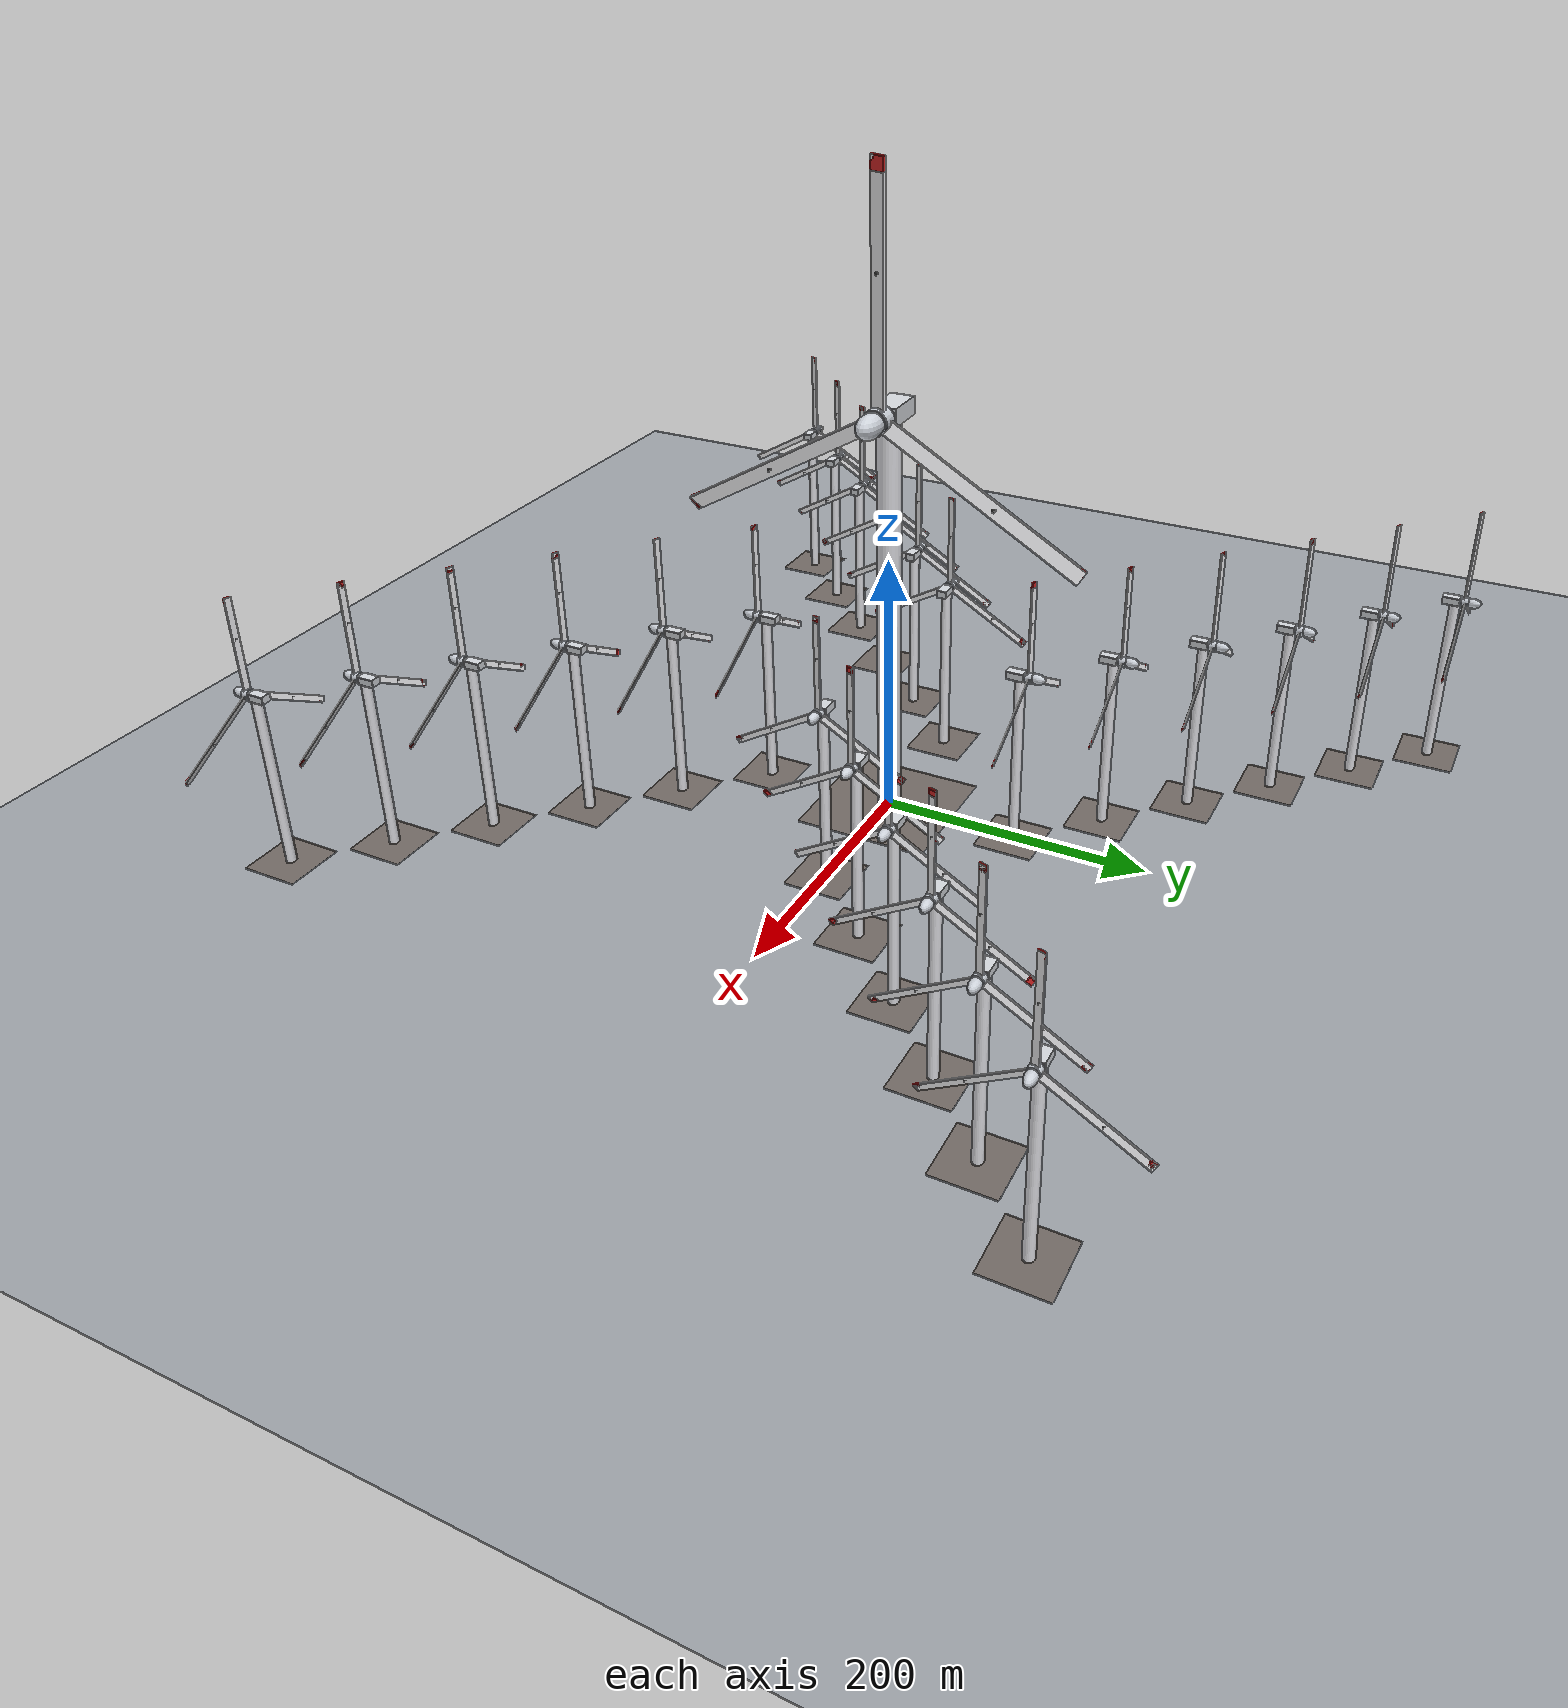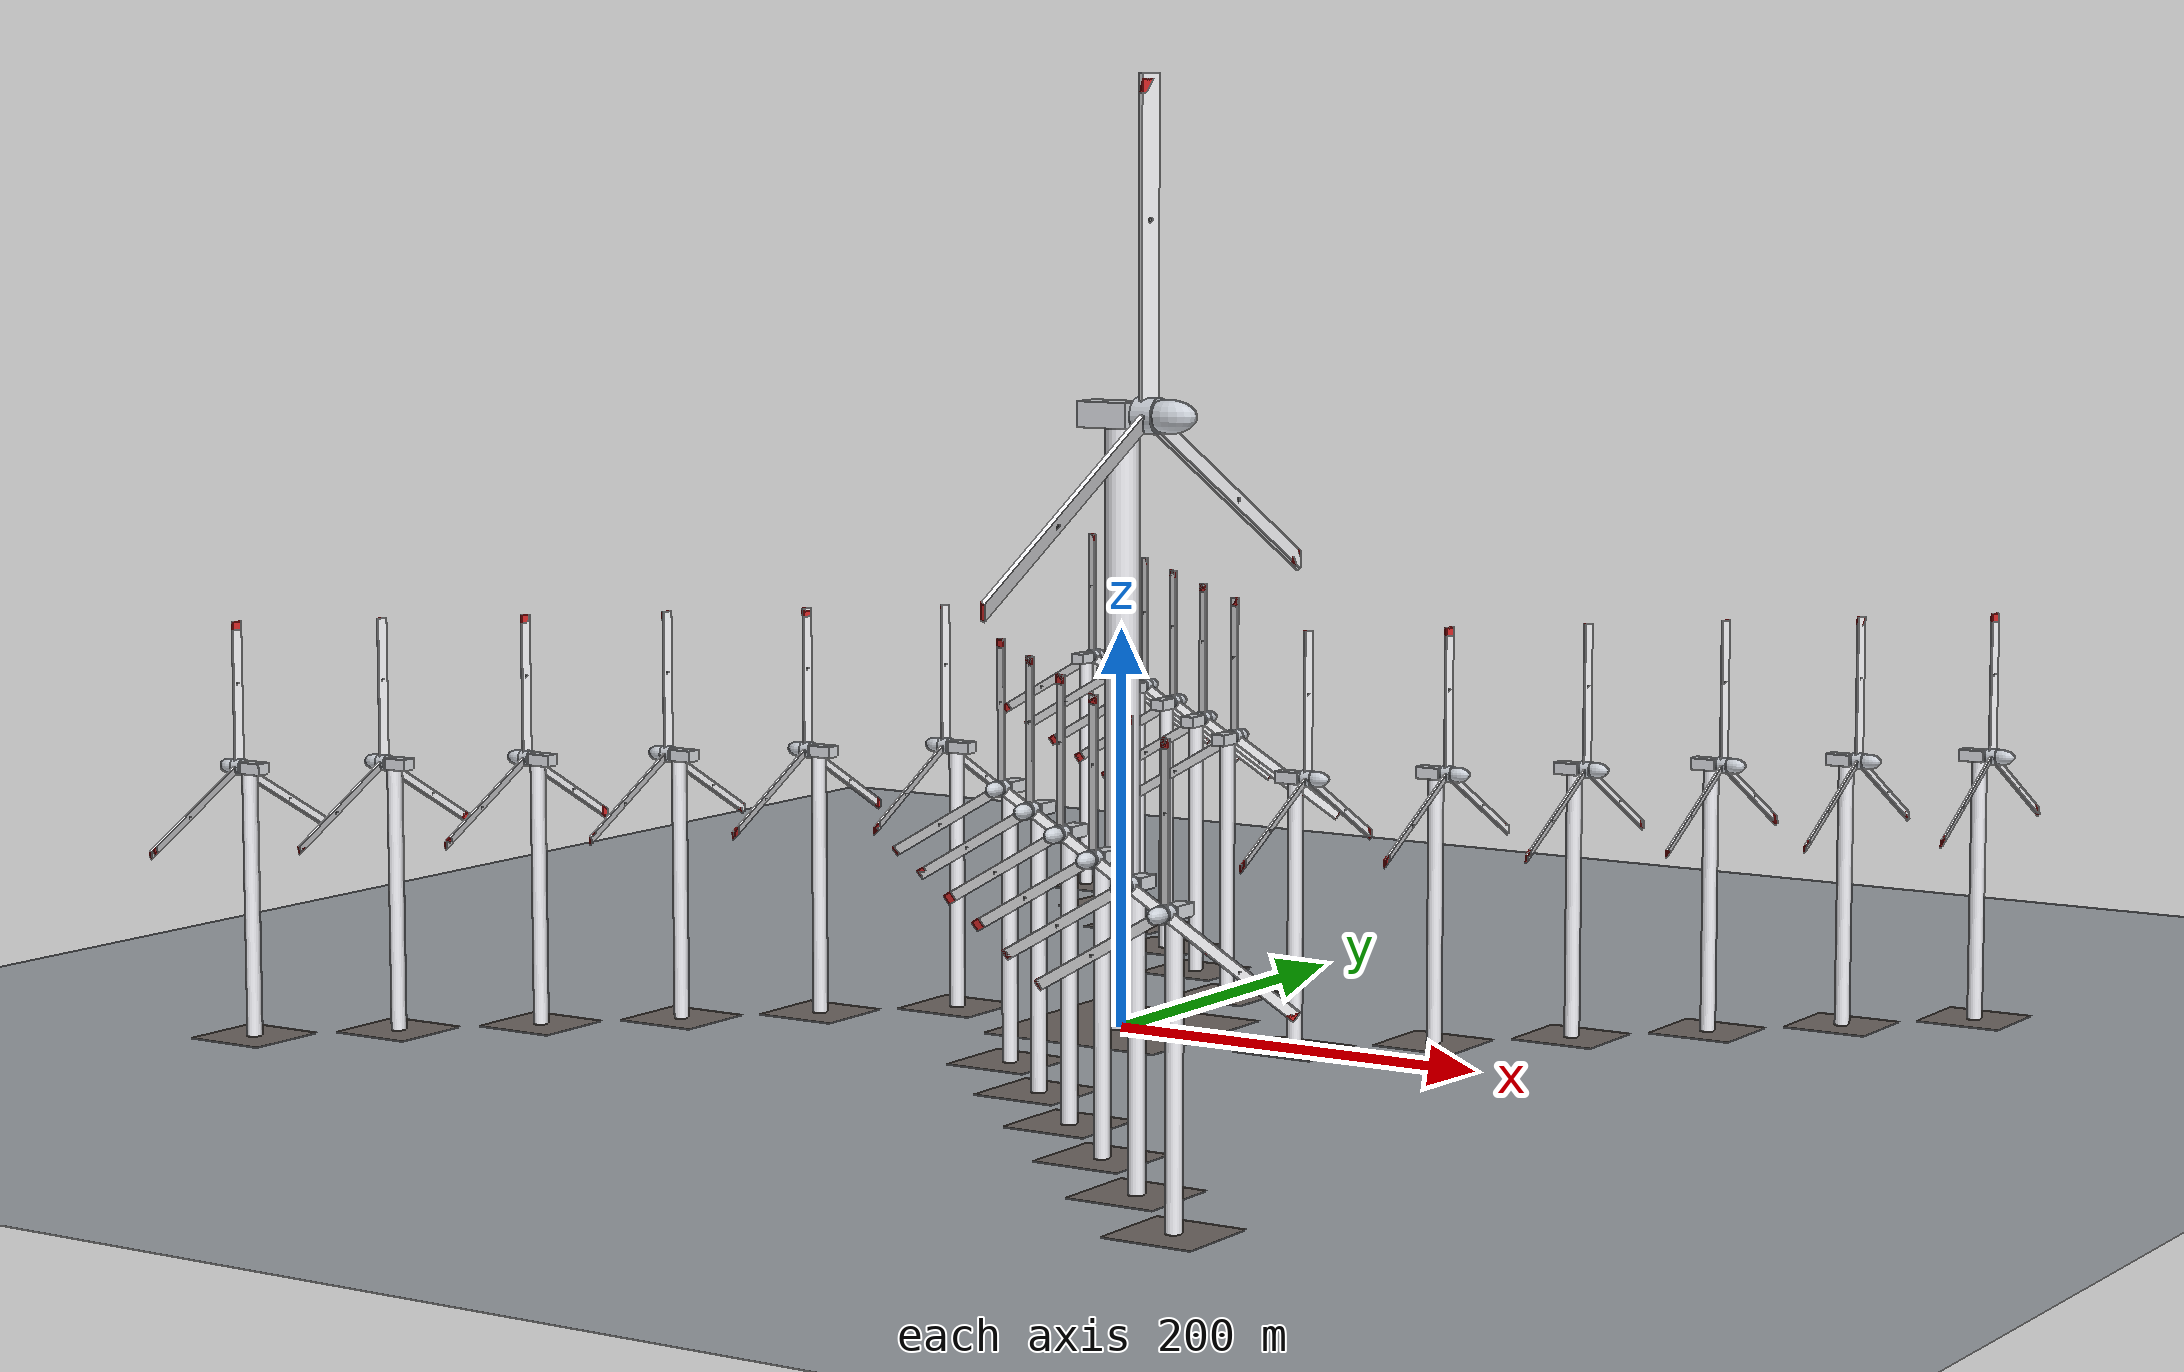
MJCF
<?xml version="1.0" encoding="UTF-8"?>
<!-- Auto-generated by wind_farm_export.py (25 turbines, all farms). Do not hand-edit. -->
<mujoco model="wind_turbines">

  <compiler eulerseq="xyz" angle="degree"/>
  <option gravity="0 0 -9.81" timestep="0.002" integrator="implicitfast"/>

  <visual>
    <global offwidth="1280" offheight="1280"/>
    <headlight diffuse="0.7 0.7 0.7" ambient="0.35 0.35 0.35" specular="0.2 0.2 0.2"/>
    <rgba haze="0.55 0.7 0.85 1"/>
    <quality shadowsize="4096"/>
  </visual>

  <default>
    <default class="rotor">
      <joint type="hinge" axis="1 0 0" limited="false" damping="0.25" frictionloss="0.02"/>
    </default>
    <default class="yaw">
      <joint type="hinge" axis="0 0 1" limited="false" damping="0.25" frictionloss="0.02"/>
    </default>
    <geom contype="0" conaffinity="0"/>
  </default>

  <asset>
    <texture type="skybox" builtin="gradient" rgb1="0.5 0.7 0.95" rgb2="0.05 0.1 0.2" width="512" height="512"/>
    <texture name="ground_tex" type="2d" builtin="checker"
             rgb1="0.7 0.72 0.74" rgb2="0.55 0.57 0.6" width="300" height="300"/>
    <material name="ground_mat"  texture="ground_tex" texrepeat="40 40" reflectance="0.15"/>
    <material name="tower_mat"   rgba="0.93 0.93 0.95 1" specular="0.4" shininess="0.4"/>
    <material name="base_mat"    rgba="0.45 0.42 0.4  1" specular="0.1"/>
    <material name="nacelle_mat" rgba="0.85 0.86 0.88 1" specular="0.5" shininess="0.5"/>
    <material name="hub_mat"     rgba="0.8  0.82 0.85 1" specular="0.6" shininess="0.6"/>
    <material name="blade_mat"   rgba="0.96 0.96 0.97 1" specular="0.5" shininess="0.5"/>
    <material name="tip_mat"     rgba="0.85 0.15 0.15 1"/>
  </asset>

  <worldbody>
    <light name="sun" pos="0 0 596.5" dir="0 0 -1" directional="true"
           diffuse="0.6 0.6 0.6" specular="0.3 0.3 0.3"/>
    <geom name="ground" type="plane" size="596.5 596.5 0.1" material="ground_mat" contype="1" conaffinity="1"/>

    <!-- Farm_East_1 | tower_height = 131 | pos (100, 0) | initial yaw 0 deg -->
    <body name="Farm_East_1_base" pos="100 0 0.1" euler="0 0 0">
      <geom name="Farm_East_1_tower_base" type="box" size="21.8333 21.8333 0.1" pos="0 0 0" material="base_mat"/>
      <geom name="Farm_East_1_tower" type="cylinder" size="3.73587 65.5" pos="0 0 65.6" material="tower_mat"/>

      <body name="Farm_East_1_nacelle" pos="0 0 133.911">
        <joint name="Farm_East_1_yaw" class="yaw"/>
        <geom name="Farm_East_1_nacelle_geom" type="box" size="6.21954 3.73587 2.81123" pos="-3.10977 0 0" material="nacelle_mat"/>

        <body name="Farm_East_1_hub" pos="6.84564 0 0">
          <joint name="Farm_East_1_rotor" class="rotor"/>
          <geom name="Farm_East_1_hub_geom" type="cylinder" size="3.93 2.62" euler="0 90 0" pos="0 0 0" material="hub_mat"/>
          <geom name="Farm_East_1_spinner" type="ellipsoid" size="6.55 3.668 3.668" pos="5.24 0 0" material="hub_mat"/>

        <body name="Farm_East_1_blade1" euler="-120 0 -18">
          <geom name="Farm_East_1_blade1_geom" type="box" size="0.524 2.358 34.5625" pos="0 0 37.3737" material="blade_mat"/>
          <geom name="Farm_East_1_blade1_tip" type="box" size="0.524 2.358 2.07375" pos="0 0 69.8625" material="tip_mat"/>
          <site name="Farm_East_1_blade1_aero" pos="0 0 41.1756" size="0.786"/>
        </body>
        <body name="Farm_East_1_blade2" euler="120 0 -18">
          <geom name="Farm_East_1_blade2_geom" type="box" size="0.524 2.358 34.5625" pos="0 0 37.3737" material="blade_mat"/>
          <geom name="Farm_East_1_blade2_tip" type="box" size="0.524 2.358 2.07375" pos="0 0 69.8625" material="tip_mat"/>
          <site name="Farm_East_1_blade2_aero" pos="0 0 41.1756" size="0.786"/>
        </body>
        <body name="Farm_East_1_blade3" euler="0 0 -18">
          <geom name="Farm_East_1_blade3_geom" type="box" size="0.524 2.358 34.5625" pos="0 0 37.3737" material="blade_mat"/>
          <geom name="Farm_East_1_blade3_tip" type="box" size="0.524 2.358 2.07375" pos="0 0 69.8625" material="tip_mat"/>
          <site name="Farm_East_1_blade3_aero" pos="0 0 41.1756" size="0.786"/>
        </body>
        </body>
      </body>
    </body>

    <!-- Farm_East_2 | tower_height = 131 | pos (150, 50) | initial yaw 0 deg -->
    <body name="Farm_East_2_base" pos="150 50 0.1" euler="0 0 0">
      <geom name="Farm_East_2_tower_base" type="box" size="21.8333 21.8333 0.1" pos="0 0 0" material="base_mat"/>
      <geom name="Farm_East_2_tower" type="cylinder" size="3.73587 65.5" pos="0 0 65.6" material="tower_mat"/>

      <body name="Farm_East_2_nacelle" pos="0 0 133.911">
        <joint name="Farm_East_2_yaw" class="yaw"/>
        <geom name="Farm_East_2_nacelle_geom" type="box" size="6.21954 3.73587 2.81123" pos="-3.10977 0 0" material="nacelle_mat"/>

        <body name="Farm_East_2_hub" pos="6.84564 0 0">
          <joint name="Farm_East_2_rotor" class="rotor"/>
          <geom name="Farm_East_2_hub_geom" type="cylinder" size="3.93 2.62" euler="0 90 0" pos="0 0 0" material="hub_mat"/>
          <geom name="Farm_East_2_spinner" type="ellipsoid" size="6.55 3.668 3.668" pos="5.24 0 0" material="hub_mat"/>

        <body name="Farm_East_2_blade1" euler="-120 0 -18">
          <geom name="Farm_East_2_blade1_geom" type="box" size="0.524 2.358 34.5625" pos="0 0 37.3737" material="blade_mat"/>
          <geom name="Farm_East_2_blade1_tip" type="box" size="0.524 2.358 2.07375" pos="0 0 69.8625" material="tip_mat"/>
          <site name="Farm_East_2_blade1_aero" pos="0 0 41.1756" size="0.786"/>
        </body>
        <body name="Farm_East_2_blade2" euler="120 0 -18">
          <geom name="Farm_East_2_blade2_geom" type="box" size="0.524 2.358 34.5625" pos="0 0 37.3737" material="blade_mat"/>
          <geom name="Farm_East_2_blade2_tip" type="box" size="0.524 2.358 2.07375" pos="0 0 69.8625" material="tip_mat"/>
          <site name="Farm_East_2_blade2_aero" pos="0 0 41.1756" size="0.786"/>
        </body>
        <body name="Farm_East_2_blade3" euler="0 0 -18">
          <geom name="Farm_East_2_blade3_geom" type="box" size="0.524 2.358 34.5625" pos="0 0 37.3737" material="blade_mat"/>
          <geom name="Farm_East_2_blade3_tip" type="box" size="0.524 2.358 2.07375" pos="0 0 69.8625" material="tip_mat"/>
          <site name="Farm_East_2_blade3_aero" pos="0 0 41.1756" size="0.786"/>
        </body>
        </body>
      </body>
    </body>

    <!-- Farm_East_3 | tower_height = 131 | pos (200, 100) | initial yaw 0 deg -->
    <body name="Farm_East_3_base" pos="200 100 0.1" euler="0 0 0">
      <geom name="Farm_East_3_tower_base" type="box" size="21.8333 21.8333 0.1" pos="0 0 0" material="base_mat"/>
      <geom name="Farm_East_3_tower" type="cylinder" size="3.73587 65.5" pos="0 0 65.6" material="tower_mat"/>

      <body name="Farm_East_3_nacelle" pos="0 0 133.911">
        <joint name="Farm_East_3_yaw" class="yaw"/>
        <geom name="Farm_East_3_nacelle_geom" type="box" size="6.21954 3.73587 2.81123" pos="-3.10977 0 0" material="nacelle_mat"/>

        <body name="Farm_East_3_hub" pos="6.84564 0 0">
          <joint name="Farm_East_3_rotor" class="rotor"/>
          <geom name="Farm_East_3_hub_geom" type="cylinder" size="3.93 2.62" euler="0 90 0" pos="0 0 0" material="hub_mat"/>
          <geom name="Farm_East_3_spinner" type="ellipsoid" size="6.55 3.668 3.668" pos="5.24 0 0" material="hub_mat"/>

        <body name="Farm_East_3_blade1" euler="-120 0 -18">
          <geom name="Farm_East_3_blade1_geom" type="box" size="0.524 2.358 34.5625" pos="0 0 37.3737" material="blade_mat"/>
          <geom name="Farm_East_3_blade1_tip" type="box" size="0.524 2.358 2.07375" pos="0 0 69.8625" material="tip_mat"/>
          <site name="Farm_East_3_blade1_aero" pos="0 0 41.1756" size="0.786"/>
        </body>
        <body name="Farm_East_3_blade2" euler="120 0 -18">
          <geom name="Farm_East_3_blade2_geom" type="box" size="0.524 2.358 34.5625" pos="0 0 37.3737" material="blade_mat"/>
          <geom name="Farm_East_3_blade2_tip" type="box" size="0.524 2.358 2.07375" pos="0 0 69.8625" material="tip_mat"/>
          <site name="Farm_East_3_blade2_aero" pos="0 0 41.1756" size="0.786"/>
        </body>
        <body name="Farm_East_3_blade3" euler="0 0 -18">
          <geom name="Farm_East_3_blade3_geom" type="box" size="0.524 2.358 34.5625" pos="0 0 37.3737" material="blade_mat"/>
          <geom name="Farm_East_3_blade3_tip" type="box" size="0.524 2.358 2.07375" pos="0 0 69.8625" material="tip_mat"/>
          <site name="Farm_East_3_blade3_aero" pos="0 0 41.1756" size="0.786"/>
        </body>
        </body>
      </body>
    </body>

    <!-- Farm_East_4 | tower_height = 131 | pos (250, 150) | initial yaw 0 deg -->
    <body name="Farm_East_4_base" pos="250 150 0.1" euler="0 0 0">
      <geom name="Farm_East_4_tower_base" type="box" size="21.8333 21.8333 0.1" pos="0 0 0" material="base_mat"/>
      <geom name="Farm_East_4_tower" type="cylinder" size="3.73587 65.5" pos="0 0 65.6" material="tower_mat"/>

      <body name="Farm_East_4_nacelle" pos="0 0 133.911">
        <joint name="Farm_East_4_yaw" class="yaw"/>
        <geom name="Farm_East_4_nacelle_geom" type="box" size="6.21954 3.73587 2.81123" pos="-3.10977 0 0" material="nacelle_mat"/>

        <body name="Farm_East_4_hub" pos="6.84564 0 0">
          <joint name="Farm_East_4_rotor" class="rotor"/>
          <geom name="Farm_East_4_hub_geom" type="cylinder" size="3.93 2.62" euler="0 90 0" pos="0 0 0" material="hub_mat"/>
          <geom name="Farm_East_4_spinner" type="ellipsoid" size="6.55 3.668 3.668" pos="5.24 0 0" material="hub_mat"/>

        <body name="Farm_East_4_blade1" euler="-120 0 -18">
          <geom name="Farm_East_4_blade1_geom" type="box" size="0.524 2.358 34.5625" pos="0 0 37.3737" material="blade_mat"/>
          <geom name="Farm_East_4_blade1_tip" type="box" size="0.524 2.358 2.07375" pos="0 0 69.8625" material="tip_mat"/>
          <site name="Farm_East_4_blade1_aero" pos="0 0 41.1756" size="0.786"/>
        </body>
        <body name="Farm_East_4_blade2" euler="120 0 -18">
          <geom name="Farm_East_4_blade2_geom" type="box" size="0.524 2.358 34.5625" pos="0 0 37.3737" material="blade_mat"/>
          <geom name="Farm_East_4_blade2_tip" type="box" size="0.524 2.358 2.07375" pos="0 0 69.8625" material="tip_mat"/>
          <site name="Farm_East_4_blade2_aero" pos="0 0 41.1756" size="0.786"/>
        </body>
        <body name="Farm_East_4_blade3" euler="0 0 -18">
          <geom name="Farm_East_4_blade3_geom" type="box" size="0.524 2.358 34.5625" pos="0 0 37.3737" material="blade_mat"/>
          <geom name="Farm_East_4_blade3_tip" type="box" size="0.524 2.358 2.07375" pos="0 0 69.8625" material="tip_mat"/>
          <site name="Farm_East_4_blade3_aero" pos="0 0 41.1756" size="0.786"/>
        </body>
        </body>
      </body>
    </body>

    <!-- Farm_East_5 | tower_height = 131 | pos (300, 200) | initial yaw 0 deg -->
    <body name="Farm_East_5_base" pos="300 200 0.1" euler="0 0 0">
      <geom name="Farm_East_5_tower_base" type="box" size="21.8333 21.8333 0.1" pos="0 0 0" material="base_mat"/>
      <geom name="Farm_East_5_tower" type="cylinder" size="3.73587 65.5" pos="0 0 65.6" material="tower_mat"/>

      <body name="Farm_East_5_nacelle" pos="0 0 133.911">
        <joint name="Farm_East_5_yaw" class="yaw"/>
        <geom name="Farm_East_5_nacelle_geom" type="box" size="6.21954 3.73587 2.81123" pos="-3.10977 0 0" material="nacelle_mat"/>

        <body name="Farm_East_5_hub" pos="6.84564 0 0">
          <joint name="Farm_East_5_rotor" class="rotor"/>
          <geom name="Farm_East_5_hub_geom" type="cylinder" size="3.93 2.62" euler="0 90 0" pos="0 0 0" material="hub_mat"/>
          <geom name="Farm_East_5_spinner" type="ellipsoid" size="6.55 3.668 3.668" pos="5.24 0 0" material="hub_mat"/>

        <body name="Farm_East_5_blade1" euler="-120 0 -18">
          <geom name="Farm_East_5_blade1_geom" type="box" size="0.524 2.358 34.5625" pos="0 0 37.3737" material="blade_mat"/>
          <geom name="Farm_East_5_blade1_tip" type="box" size="0.524 2.358 2.07375" pos="0 0 69.8625" material="tip_mat"/>
          <site name="Farm_East_5_blade1_aero" pos="0 0 41.1756" size="0.786"/>
        </body>
        <body name="Farm_East_5_blade2" euler="120 0 -18">
          <geom name="Farm_East_5_blade2_geom" type="box" size="0.524 2.358 34.5625" pos="0 0 37.3737" material="blade_mat"/>
          <geom name="Farm_East_5_blade2_tip" type="box" size="0.524 2.358 2.07375" pos="0 0 69.8625" material="tip_mat"/>
          <site name="Farm_East_5_blade2_aero" pos="0 0 41.1756" size="0.786"/>
        </body>
        <body name="Farm_East_5_blade3" euler="0 0 -18">
          <geom name="Farm_East_5_blade3_geom" type="box" size="0.524 2.358 34.5625" pos="0 0 37.3737" material="blade_mat"/>
          <geom name="Farm_East_5_blade3_tip" type="box" size="0.524 2.358 2.07375" pos="0 0 69.8625" material="tip_mat"/>
          <site name="Farm_East_5_blade3_aero" pos="0 0 41.1756" size="0.786"/>
        </body>
        </body>
      </body>
    </body>

    <!-- Farm_East_6 | tower_height = 131 | pos (350, 250) | initial yaw 0 deg -->
    <body name="Farm_East_6_base" pos="350 250 0.1" euler="0 0 0">
      <geom name="Farm_East_6_tower_base" type="box" size="21.8333 21.8333 0.1" pos="0 0 0" material="base_mat"/>
      <geom name="Farm_East_6_tower" type="cylinder" size="3.73587 65.5" pos="0 0 65.6" material="tower_mat"/>

      <body name="Farm_East_6_nacelle" pos="0 0 133.911">
        <joint name="Farm_East_6_yaw" class="yaw"/>
        <geom name="Farm_East_6_nacelle_geom" type="box" size="6.21954 3.73587 2.81123" pos="-3.10977 0 0" material="nacelle_mat"/>

        <body name="Farm_East_6_hub" pos="6.84564 0 0">
          <joint name="Farm_East_6_rotor" class="rotor"/>
          <geom name="Farm_East_6_hub_geom" type="cylinder" size="3.93 2.62" euler="0 90 0" pos="0 0 0" material="hub_mat"/>
          <geom name="Farm_East_6_spinner" type="ellipsoid" size="6.55 3.668 3.668" pos="5.24 0 0" material="hub_mat"/>

        <body name="Farm_East_6_blade1" euler="-120 0 -18">
          <geom name="Farm_East_6_blade1_geom" type="box" size="0.524 2.358 34.5625" pos="0 0 37.3737" material="blade_mat"/>
          <geom name="Farm_East_6_blade1_tip" type="box" size="0.524 2.358 2.07375" pos="0 0 69.8625" material="tip_mat"/>
          <site name="Farm_East_6_blade1_aero" pos="0 0 41.1756" size="0.786"/>
        </body>
        <body name="Farm_East_6_blade2" euler="120 0 -18">
          <geom name="Farm_East_6_blade2_geom" type="box" size="0.524 2.358 34.5625" pos="0 0 37.3737" material="blade_mat"/>
          <geom name="Farm_East_6_blade2_tip" type="box" size="0.524 2.358 2.07375" pos="0 0 69.8625" material="tip_mat"/>
          <site name="Farm_East_6_blade2_aero" pos="0 0 41.1756" size="0.786"/>
        </body>
        <body name="Farm_East_6_blade3" euler="0 0 -18">
          <geom name="Farm_East_6_blade3_geom" type="box" size="0.524 2.358 34.5625" pos="0 0 37.3737" material="blade_mat"/>
          <geom name="Farm_East_6_blade3_tip" type="box" size="0.524 2.358 2.07375" pos="0 0 69.8625" material="tip_mat"/>
          <site name="Farm_East_6_blade3_aero" pos="0 0 41.1756" size="0.786"/>
        </body>
        </body>
      </body>
    </body>

    <!-- Farm_North_1 | tower_height = 131 | pos (0, 100) | initial yaw 90 deg -->
    <body name="Farm_North_1_base" pos="0 100 0.1" euler="0 0 90">
      <geom name="Farm_North_1_tower_base" type="box" size="21.8333 21.8333 0.1" pos="0 0 0" material="base_mat"/>
      <geom name="Farm_North_1_tower" type="cylinder" size="3.73587 65.5" pos="0 0 65.6" material="tower_mat"/>

      <body name="Farm_North_1_nacelle" pos="0 0 133.911">
        <joint name="Farm_North_1_yaw" class="yaw"/>
        <geom name="Farm_North_1_nacelle_geom" type="box" size="6.21954 3.73587 2.81123" pos="-3.10977 0 0" material="nacelle_mat"/>

        <body name="Farm_North_1_hub" pos="6.84564 0 0">
          <joint name="Farm_North_1_rotor" class="rotor"/>
          <geom name="Farm_North_1_hub_geom" type="cylinder" size="3.93 2.62" euler="0 90 0" pos="0 0 0" material="hub_mat"/>
          <geom name="Farm_North_1_spinner" type="ellipsoid" size="6.55 3.668 3.668" pos="5.24 0 0" material="hub_mat"/>

        <body name="Farm_North_1_blade1" euler="-120 0 -18">
          <geom name="Farm_North_1_blade1_geom" type="box" size="0.524 2.358 34.5625" pos="0 0 37.3737" material="blade_mat"/>
          <geom name="Farm_North_1_blade1_tip" type="box" size="0.524 2.358 2.07375" pos="0 0 69.8625" material="tip_mat"/>
          <site name="Farm_North_1_blade1_aero" pos="0 0 41.1756" size="0.786"/>
        </body>
        <body name="Farm_North_1_blade2" euler="120 0 -18">
          <geom name="Farm_North_1_blade2_geom" type="box" size="0.524 2.358 34.5625" pos="0 0 37.3737" material="blade_mat"/>
          <geom name="Farm_North_1_blade2_tip" type="box" size="0.524 2.358 2.07375" pos="0 0 69.8625" material="tip_mat"/>
          <site name="Farm_North_1_blade2_aero" pos="0 0 41.1756" size="0.786"/>
        </body>
        <body name="Farm_North_1_blade3" euler="0 0 -18">
          <geom name="Farm_North_1_blade3_geom" type="box" size="0.524 2.358 34.5625" pos="0 0 37.3737" material="blade_mat"/>
          <geom name="Farm_North_1_blade3_tip" type="box" size="0.524 2.358 2.07375" pos="0 0 69.8625" material="tip_mat"/>
          <site name="Farm_North_1_blade3_aero" pos="0 0 41.1756" size="0.786"/>
        </body>
        </body>
      </body>
    </body>

    <!-- Farm_North_2 | tower_height = 131 | pos (-50, 150) | initial yaw 90 deg -->
    <body name="Farm_North_2_base" pos="-50 150 0.1" euler="0 0 90">
      <geom name="Farm_North_2_tower_base" type="box" size="21.8333 21.8333 0.1" pos="0 0 0" material="base_mat"/>
      <geom name="Farm_North_2_tower" type="cylinder" size="3.73587 65.5" pos="0 0 65.6" material="tower_mat"/>

      <body name="Farm_North_2_nacelle" pos="0 0 133.911">
        <joint name="Farm_North_2_yaw" class="yaw"/>
        <geom name="Farm_North_2_nacelle_geom" type="box" size="6.21954 3.73587 2.81123" pos="-3.10977 0 0" material="nacelle_mat"/>

        <body name="Farm_North_2_hub" pos="6.84564 0 0">
          <joint name="Farm_North_2_rotor" class="rotor"/>
          <geom name="Farm_North_2_hub_geom" type="cylinder" size="3.93 2.62" euler="0 90 0" pos="0 0 0" material="hub_mat"/>
          <geom name="Farm_North_2_spinner" type="ellipsoid" size="6.55 3.668 3.668" pos="5.24 0 0" material="hub_mat"/>

        <body name="Farm_North_2_blade1" euler="-120 0 -18">
          <geom name="Farm_North_2_blade1_geom" type="box" size="0.524 2.358 34.5625" pos="0 0 37.3737" material="blade_mat"/>
          <geom name="Farm_North_2_blade1_tip" type="box" size="0.524 2.358 2.07375" pos="0 0 69.8625" material="tip_mat"/>
          <site name="Farm_North_2_blade1_aero" pos="0 0 41.1756" size="0.786"/>
        </body>
        <body name="Farm_North_2_blade2" euler="120 0 -18">
          <geom name="Farm_North_2_blade2_geom" type="box" size="0.524 2.358 34.5625" pos="0 0 37.3737" material="blade_mat"/>
          <geom name="Farm_North_2_blade2_tip" type="box" size="0.524 2.358 2.07375" pos="0 0 69.8625" material="tip_mat"/>
          <site name="Farm_North_2_blade2_aero" pos="0 0 41.1756" size="0.786"/>
        </body>
        <body name="Farm_North_2_blade3" euler="0 0 -18">
          <geom name="Farm_North_2_blade3_geom" type="box" size="0.524 2.358 34.5625" pos="0 0 37.3737" material="blade_mat"/>
          <geom name="Farm_North_2_blade3_tip" type="box" size="0.524 2.358 2.07375" pos="0 0 69.8625" material="tip_mat"/>
          <site name="Farm_North_2_blade3_aero" pos="0 0 41.1756" size="0.786"/>
        </body>
        </body>
      </body>
    </body>

    <!-- Farm_North_3 | tower_height = 131 | pos (-100, 200) | initial yaw 90 deg -->
    <body name="Farm_North_3_base" pos="-100 200 0.1" euler="0 0 90">
      <geom name="Farm_North_3_tower_base" type="box" size="21.8333 21.8333 0.1" pos="0 0 0" material="base_mat"/>
      <geom name="Farm_North_3_tower" type="cylinder" size="3.73587 65.5" pos="0 0 65.6" material="tower_mat"/>

      <body name="Farm_North_3_nacelle" pos="0 0 133.911">
        <joint name="Farm_North_3_yaw" class="yaw"/>
        <geom name="Farm_North_3_nacelle_geom" type="box" size="6.21954 3.73587 2.81123" pos="-3.10977 0 0" material="nacelle_mat"/>

        <body name="Farm_North_3_hub" pos="6.84564 0 0">
          <joint name="Farm_North_3_rotor" class="rotor"/>
          <geom name="Farm_North_3_hub_geom" type="cylinder" size="3.93 2.62" euler="0 90 0" pos="0 0 0" material="hub_mat"/>
          <geom name="Farm_North_3_spinner" type="ellipsoid" size="6.55 3.668 3.668" pos="5.24 0 0" material="hub_mat"/>

        <body name="Farm_North_3_blade1" euler="-120 0 -18">
          <geom name="Farm_North_3_blade1_geom" type="box" size="0.524 2.358 34.5625" pos="0 0 37.3737" material="blade_mat"/>
          <geom name="Farm_North_3_blade1_tip" type="box" size="0.524 2.358 2.07375" pos="0 0 69.8625" material="tip_mat"/>
          <site name="Farm_North_3_blade1_aero" pos="0 0 41.1756" size="0.786"/>
        </body>
        <body name="Farm_North_3_blade2" euler="120 0 -18">
          <geom name="Farm_North_3_blade2_geom" type="box" size="0.524 2.358 34.5625" pos="0 0 37.3737" material="blade_mat"/>
          <geom name="Farm_North_3_blade2_tip" type="box" size="0.524 2.358 2.07375" pos="0 0 69.8625" material="tip_mat"/>
          <site name="Farm_North_3_blade2_aero" pos="0 0 41.1756" size="0.786"/>
        </body>
        <body name="Farm_North_3_blade3" euler="0 0 -18">
          <geom name="Farm_North_3_blade3_geom" type="box" size="0.524 2.358 34.5625" pos="0 0 37.3737" material="blade_mat"/>
          <geom name="Farm_North_3_blade3_tip" type="box" size="0.524 2.358 2.07375" pos="0 0 69.8625" material="tip_mat"/>
          <site name="Farm_North_3_blade3_aero" pos="0 0 41.1756" size="0.786"/>
        </body>
        </body>
      </body>
    </body>

    <!-- Farm_North_4 | tower_height = 131 | pos (-150, 250) | initial yaw 90 deg -->
    <body name="Farm_North_4_base" pos="-150 250 0.1" euler="0 0 90">
      <geom name="Farm_North_4_tower_base" type="box" size="21.8333 21.8333 0.1" pos="0 0 0" material="base_mat"/>
      <geom name="Farm_North_4_tower" type="cylinder" size="3.73587 65.5" pos="0 0 65.6" material="tower_mat"/>

      <body name="Farm_North_4_nacelle" pos="0 0 133.911">
        <joint name="Farm_North_4_yaw" class="yaw"/>
        <geom name="Farm_North_4_nacelle_geom" type="box" size="6.21954 3.73587 2.81123" pos="-3.10977 0 0" material="nacelle_mat"/>

        <body name="Farm_North_4_hub" pos="6.84564 0 0">
          <joint name="Farm_North_4_rotor" class="rotor"/>
          <geom name="Farm_North_4_hub_geom" type="cylinder" size="3.93 2.62" euler="0 90 0" pos="0 0 0" material="hub_mat"/>
          <geom name="Farm_North_4_spinner" type="ellipsoid" size="6.55 3.668 3.668" pos="5.24 0 0" material="hub_mat"/>

        <body name="Farm_North_4_blade1" euler="-120 0 -18">
          <geom name="Farm_North_4_blade1_geom" type="box" size="0.524 2.358 34.5625" pos="0 0 37.3737" material="blade_mat"/>
          <geom name="Farm_North_4_blade1_tip" type="box" size="0.524 2.358 2.07375" pos="0 0 69.8625" material="tip_mat"/>
          <site name="Farm_North_4_blade1_aero" pos="0 0 41.1756" size="0.786"/>
        </body>
        <body name="Farm_North_4_blade2" euler="120 0 -18">
          <geom name="Farm_North_4_blade2_geom" type="box" size="0.524 2.358 34.5625" pos="0 0 37.3737" material="blade_mat"/>
          <geom name="Farm_North_4_blade2_tip" type="box" size="0.524 2.358 2.07375" pos="0 0 69.8625" material="tip_mat"/>
          <site name="Farm_North_4_blade2_aero" pos="0 0 41.1756" size="0.786"/>
        </body>
        <body name="Farm_North_4_blade3" euler="0 0 -18">
          <geom name="Farm_North_4_blade3_geom" type="box" size="0.524 2.358 34.5625" pos="0 0 37.3737" material="blade_mat"/>
          <geom name="Farm_North_4_blade3_tip" type="box" size="0.524 2.358 2.07375" pos="0 0 69.8625" material="tip_mat"/>
          <site name="Farm_North_4_blade3_aero" pos="0 0 41.1756" size="0.786"/>
        </body>
        </body>
      </body>
    </body>

    <!-- Farm_North_5 | tower_height = 131 | pos (-200, 300) | initial yaw 90 deg -->
    <body name="Farm_North_5_base" pos="-200 300 0.1" euler="0 0 90">
      <geom name="Farm_North_5_tower_base" type="box" size="21.8333 21.8333 0.1" pos="0 0 0" material="base_mat"/>
      <geom name="Farm_North_5_tower" type="cylinder" size="3.73587 65.5" pos="0 0 65.6" material="tower_mat"/>

      <body name="Farm_North_5_nacelle" pos="0 0 133.911">
        <joint name="Farm_North_5_yaw" class="yaw"/>
        <geom name="Farm_North_5_nacelle_geom" type="box" size="6.21954 3.73587 2.81123" pos="-3.10977 0 0" material="nacelle_mat"/>

        <body name="Farm_North_5_hub" pos="6.84564 0 0">
          <joint name="Farm_North_5_rotor" class="rotor"/>
          <geom name="Farm_North_5_hub_geom" type="cylinder" size="3.93 2.62" euler="0 90 0" pos="0 0 0" material="hub_mat"/>
          <geom name="Farm_North_5_spinner" type="ellipsoid" size="6.55 3.668 3.668" pos="5.24 0 0" material="hub_mat"/>

        <body name="Farm_North_5_blade1" euler="-120 0 -18">
          <geom name="Farm_North_5_blade1_geom" type="box" size="0.524 2.358 34.5625" pos="0 0 37.3737" material="blade_mat"/>
          <geom name="Farm_North_5_blade1_tip" type="box" size="0.524 2.358 2.07375" pos="0 0 69.8625" material="tip_mat"/>
          <site name="Farm_North_5_blade1_aero" pos="0 0 41.1756" size="0.786"/>
        </body>
        <body name="Farm_North_5_blade2" euler="120 0 -18">
          <geom name="Farm_North_5_blade2_geom" type="box" size="0.524 2.358 34.5625" pos="0 0 37.3737" material="blade_mat"/>
          <geom name="Farm_North_5_blade2_tip" type="box" size="0.524 2.358 2.07375" pos="0 0 69.8625" material="tip_mat"/>
          <site name="Farm_North_5_blade2_aero" pos="0 0 41.1756" size="0.786"/>
        </body>
        <body name="Farm_North_5_blade3" euler="0 0 -18">
          <geom name="Farm_North_5_blade3_geom" type="box" size="0.524 2.358 34.5625" pos="0 0 37.3737" material="blade_mat"/>
          <geom name="Farm_North_5_blade3_tip" type="box" size="0.524 2.358 2.07375" pos="0 0 69.8625" material="tip_mat"/>
          <site name="Farm_North_5_blade3_aero" pos="0 0 41.1756" size="0.786"/>
        </body>
        </body>
      </body>
    </body>

    <!-- Farm_North_6 | tower_height = 131 | pos (-250, 350) | initial yaw 90 deg -->
    <body name="Farm_North_6_base" pos="-250 350 0.1" euler="0 0 90">
      <geom name="Farm_North_6_tower_base" type="box" size="21.8333 21.8333 0.1" pos="0 0 0" material="base_mat"/>
      <geom name="Farm_North_6_tower" type="cylinder" size="3.73587 65.5" pos="0 0 65.6" material="tower_mat"/>

      <body name="Farm_North_6_nacelle" pos="0 0 133.911">
        <joint name="Farm_North_6_yaw" class="yaw"/>
        <geom name="Farm_North_6_nacelle_geom" type="box" size="6.21954 3.73587 2.81123" pos="-3.10977 0 0" material="nacelle_mat"/>

        <body name="Farm_North_6_hub" pos="6.84564 0 0">
          <joint name="Farm_North_6_rotor" class="rotor"/>
          <geom name="Farm_North_6_hub_geom" type="cylinder" size="3.93 2.62" euler="0 90 0" pos="0 0 0" material="hub_mat"/>
          <geom name="Farm_North_6_spinner" type="ellipsoid" size="6.55 3.668 3.668" pos="5.24 0 0" material="hub_mat"/>

        <body name="Farm_North_6_blade1" euler="-120 0 -18">
          <geom name="Farm_North_6_blade1_geom" type="box" size="0.524 2.358 34.5625" pos="0 0 37.3737" material="blade_mat"/>
          <geom name="Farm_North_6_blade1_tip" type="box" size="0.524 2.358 2.07375" pos="0 0 69.8625" material="tip_mat"/>
          <site name="Farm_North_6_blade1_aero" pos="0 0 41.1756" size="0.786"/>
        </body>
        <body name="Farm_North_6_blade2" euler="120 0 -18">
          <geom name="Farm_North_6_blade2_geom" type="box" size="0.524 2.358 34.5625" pos="0 0 37.3737" material="blade_mat"/>
          <geom name="Farm_North_6_blade2_tip" type="box" size="0.524 2.358 2.07375" pos="0 0 69.8625" material="tip_mat"/>
          <site name="Farm_North_6_blade2_aero" pos="0 0 41.1756" size="0.786"/>
        </body>
        <body name="Farm_North_6_blade3" euler="0 0 -18">
          <geom name="Farm_North_6_blade3_geom" type="box" size="0.524 2.358 34.5625" pos="0 0 37.3737" material="blade_mat"/>
          <geom name="Farm_North_6_blade3_tip" type="box" size="0.524 2.358 2.07375" pos="0 0 69.8625" material="tip_mat"/>
          <site name="Farm_North_6_blade3_aero" pos="0 0 41.1756" size="0.786"/>
        </body>
        </body>
      </body>
    </body>

    <!-- Farm_West_1 | tower_height = 131 | pos (-100, 0) | initial yaw 180 deg -->
    <body name="Farm_West_1_base" pos="-100 0 0.1" euler="0 0 180">
      <geom name="Farm_West_1_tower_base" type="box" size="21.8333 21.8333 0.1" pos="0 0 0" material="base_mat"/>
      <geom name="Farm_West_1_tower" type="cylinder" size="3.73587 65.5" pos="0 0 65.6" material="tower_mat"/>

      <body name="Farm_West_1_nacelle" pos="0 0 133.911">
        <joint name="Farm_West_1_yaw" class="yaw"/>
        <geom name="Farm_West_1_nacelle_geom" type="box" size="6.21954 3.73587 2.81123" pos="-3.10977 0 0" material="nacelle_mat"/>

        <body name="Farm_West_1_hub" pos="6.84564 0 0">
          <joint name="Farm_West_1_rotor" class="rotor"/>
          <geom name="Farm_West_1_hub_geom" type="cylinder" size="3.93 2.62" euler="0 90 0" pos="0 0 0" material="hub_mat"/>
          <geom name="Farm_West_1_spinner" type="ellipsoid" size="6.55 3.668 3.668" pos="5.24 0 0" material="hub_mat"/>

        <body name="Farm_West_1_blade1" euler="-120 0 -18">
          <geom name="Farm_West_1_blade1_geom" type="box" size="0.524 2.358 34.5625" pos="0 0 37.3737" material="blade_mat"/>
          <geom name="Farm_West_1_blade1_tip" type="box" size="0.524 2.358 2.07375" pos="0 0 69.8625" material="tip_mat"/>
          <site name="Farm_West_1_blade1_aero" pos="0 0 41.1756" size="0.786"/>
        </body>
        <body name="Farm_West_1_blade2" euler="120 0 -18">
          <geom name="Farm_West_1_blade2_geom" type="box" size="0.524 2.358 34.5625" pos="0 0 37.3737" material="blade_mat"/>
          <geom name="Farm_West_1_blade2_tip" type="box" size="0.524 2.358 2.07375" pos="0 0 69.8625" material="tip_mat"/>
          <site name="Farm_West_1_blade2_aero" pos="0 0 41.1756" size="0.786"/>
        </body>
        <body name="Farm_West_1_blade3" euler="0 0 -18">
          <geom name="Farm_West_1_blade3_geom" type="box" size="0.524 2.358 34.5625" pos="0 0 37.3737" material="blade_mat"/>
          <geom name="Farm_West_1_blade3_tip" type="box" size="0.524 2.358 2.07375" pos="0 0 69.8625" material="tip_mat"/>
          <site name="Farm_West_1_blade3_aero" pos="0 0 41.1756" size="0.786"/>
        </body>
        </body>
      </body>
    </body>

    <!-- Farm_West_2 | tower_height = 131 | pos (-150, -50) | initial yaw 180 deg -->
    <body name="Farm_West_2_base" pos="-150 -50 0.1" euler="0 0 180">
      <geom name="Farm_West_2_tower_base" type="box" size="21.8333 21.8333 0.1" pos="0 0 0" material="base_mat"/>
      <geom name="Farm_West_2_tower" type="cylinder" size="3.73587 65.5" pos="0 0 65.6" material="tower_mat"/>

      <body name="Farm_West_2_nacelle" pos="0 0 133.911">
        <joint name="Farm_West_2_yaw" class="yaw"/>
        <geom name="Farm_West_2_nacelle_geom" type="box" size="6.21954 3.73587 2.81123" pos="-3.10977 0 0" material="nacelle_mat"/>

        <body name="Farm_West_2_hub" pos="6.84564 0 0">
          <joint name="Farm_West_2_rotor" class="rotor"/>
          <geom name="Farm_West_2_hub_geom" type="cylinder" size="3.93 2.62" euler="0 90 0" pos="0 0 0" material="hub_mat"/>
          <geom name="Farm_West_2_spinner" type="ellipsoid" size="6.55 3.668 3.668" pos="5.24 0 0" material="hub_mat"/>

        <body name="Farm_West_2_blade1" euler="-120 0 -18">
          <geom name="Farm_West_2_blade1_geom" type="box" size="0.524 2.358 34.5625" pos="0 0 37.3737" material="blade_mat"/>
          <geom name="Farm_West_2_blade1_tip" type="box" size="0.524 2.358 2.07375" pos="0 0 69.8625" material="tip_mat"/>
          <site name="Farm_West_2_blade1_aero" pos="0 0 41.1756" size="0.786"/>
        </body>
        <body name="Farm_West_2_blade2" euler="120 0 -18">
          <geom name="Farm_West_2_blade2_geom" type="box" size="0.524 2.358 34.5625" pos="0 0 37.3737" material="blade_mat"/>
          <geom name="Farm_West_2_blade2_tip" type="box" size="0.524 2.358 2.07375" pos="0 0 69.8625" material="tip_mat"/>
          <site name="Farm_West_2_blade2_aero" pos="0 0 41.1756" size="0.786"/>
        </body>
        <body name="Farm_West_2_blade3" euler="0 0 -18">
          <geom name="Farm_West_2_blade3_geom" type="box" size="0.524 2.358 34.5625" pos="0 0 37.3737" material="blade_mat"/>
          <geom name="Farm_West_2_blade3_tip" type="box" size="0.524 2.358 2.07375" pos="0 0 69.8625" material="tip_mat"/>
          <site name="Farm_West_2_blade3_aero" pos="0 0 41.1756" size="0.786"/>
        </body>
        </body>
      </body>
    </body>

    <!-- Farm_West_3 | tower_height = 131 | pos (-200, -100) | initial yaw 180 deg -->
    <body name="Farm_West_3_base" pos="-200 -100 0.1" euler="0 0 180">
      <geom name="Farm_West_3_tower_base" type="box" size="21.8333 21.8333 0.1" pos="0 0 0" material="base_mat"/>
      <geom name="Farm_West_3_tower" type="cylinder" size="3.73587 65.5" pos="0 0 65.6" material="tower_mat"/>

      <body name="Farm_West_3_nacelle" pos="0 0 133.911">
        <joint name="Farm_West_3_yaw" class="yaw"/>
        <geom name="Farm_West_3_nacelle_geom" type="box" size="6.21954 3.73587 2.81123" pos="-3.10977 0 0" material="nacelle_mat"/>

        <body name="Farm_West_3_hub" pos="6.84564 0 0">
          <joint name="Farm_West_3_rotor" class="rotor"/>
          <geom name="Farm_West_3_hub_geom" type="cylinder" size="3.93 2.62" euler="0 90 0" pos="0 0 0" material="hub_mat"/>
          <geom name="Farm_West_3_spinner" type="ellipsoid" size="6.55 3.668 3.668" pos="5.24 0 0" material="hub_mat"/>

        <body name="Farm_West_3_blade1" euler="-120 0 -18">
          <geom name="Farm_West_3_blade1_geom" type="box" size="0.524 2.358 34.5625" pos="0 0 37.3737" material="blade_mat"/>
          <geom name="Farm_West_3_blade1_tip" type="box" size="0.524 2.358 2.07375" pos="0 0 69.8625" material="tip_mat"/>
          <site name="Farm_West_3_blade1_aero" pos="0 0 41.1756" size="0.786"/>
        </body>
        <body name="Farm_West_3_blade2" euler="120 0 -18">
          <geom name="Farm_West_3_blade2_geom" type="box" size="0.524 2.358 34.5625" pos="0 0 37.3737" material="blade_mat"/>
          <geom name="Farm_West_3_blade2_tip" type="box" size="0.524 2.358 2.07375" pos="0 0 69.8625" material="tip_mat"/>
          <site name="Farm_West_3_blade2_aero" pos="0 0 41.1756" size="0.786"/>
        </body>
        <body name="Farm_West_3_blade3" euler="0 0 -18">
          <geom name="Farm_West_3_blade3_geom" type="box" size="0.524 2.358 34.5625" pos="0 0 37.3737" material="blade_mat"/>
          <geom name="Farm_West_3_blade3_tip" type="box" size="0.524 2.358 2.07375" pos="0 0 69.8625" material="tip_mat"/>
          <site name="Farm_West_3_blade3_aero" pos="0 0 41.1756" size="0.786"/>
        </body>
        </body>
      </body>
    </body>

    <!-- Farm_West_4 | tower_height = 131 | pos (-250, -150) | initial yaw 180 deg -->
    <body name="Farm_West_4_base" pos="-250 -150 0.1" euler="0 0 180">
      <geom name="Farm_West_4_tower_base" type="box" size="21.8333 21.8333 0.1" pos="0 0 0" material="base_mat"/>
      <geom name="Farm_West_4_tower" type="cylinder" size="3.73587 65.5" pos="0 0 65.6" material="tower_mat"/>

      <body name="Farm_West_4_nacelle" pos="0 0 133.911">
        <joint name="Farm_West_4_yaw" class="yaw"/>
        <geom name="Farm_West_4_nacelle_geom" type="box" size="6.21954 3.73587 2.81123" pos="-3.10977 0 0" material="nacelle_mat"/>

        <body name="Farm_West_4_hub" pos="6.84564 0 0">
          <joint name="Farm_West_4_rotor" class="rotor"/>
          <geom name="Farm_West_4_hub_geom" type="cylinder" size="3.93 2.62" euler="0 90 0" pos="0 0 0" material="hub_mat"/>
          <geom name="Farm_West_4_spinner" type="ellipsoid" size="6.55 3.668 3.668" pos="5.24 0 0" material="hub_mat"/>

        <body name="Farm_West_4_blade1" euler="-120 0 -18">
          <geom name="Farm_West_4_blade1_geom" type="box" size="0.524 2.358 34.5625" pos="0 0 37.3737" material="blade_mat"/>
          <geom name="Farm_West_4_blade1_tip" type="box" size="0.524 2.358 2.07375" pos="0 0 69.8625" material="tip_mat"/>
          <site name="Farm_West_4_blade1_aero" pos="0 0 41.1756" size="0.786"/>
        </body>
        <body name="Farm_West_4_blade2" euler="120 0 -18">
          <geom name="Farm_West_4_blade2_geom" type="box" size="0.524 2.358 34.5625" pos="0 0 37.3737" material="blade_mat"/>
          <geom name="Farm_West_4_blade2_tip" type="box" size="0.524 2.358 2.07375" pos="0 0 69.8625" material="tip_mat"/>
          <site name="Farm_West_4_blade2_aero" pos="0 0 41.1756" size="0.786"/>
        </body>
        <body name="Farm_West_4_blade3" euler="0 0 -18">
          <geom name="Farm_West_4_blade3_geom" type="box" size="0.524 2.358 34.5625" pos="0 0 37.3737" material="blade_mat"/>
          <geom name="Farm_West_4_blade3_tip" type="box" size="0.524 2.358 2.07375" pos="0 0 69.8625" material="tip_mat"/>
          <site name="Farm_West_4_blade3_aero" pos="0 0 41.1756" size="0.786"/>
        </body>
        </body>
      </body>
    </body>

    <!-- Farm_West_5 | tower_height = 131 | pos (-300, -200) | initial yaw 180 deg -->
    <body name="Farm_West_5_base" pos="-300 -200 0.1" euler="0 0 180">
      <geom name="Farm_West_5_tower_base" type="box" size="21.8333 21.8333 0.1" pos="0 0 0" material="base_mat"/>
      <geom name="Farm_West_5_tower" type="cylinder" size="3.73587 65.5" pos="0 0 65.6" material="tower_mat"/>

      <body name="Farm_West_5_nacelle" pos="0 0 133.911">
        <joint name="Farm_West_5_yaw" class="yaw"/>
        <geom name="Farm_West_5_nacelle_geom" type="box" size="6.21954 3.73587 2.81123" pos="-3.10977 0 0" material="nacelle_mat"/>

        <body name="Farm_West_5_hub" pos="6.84564 0 0">
          <joint name="Farm_West_5_rotor" class="rotor"/>
          <geom name="Farm_West_5_hub_geom" type="cylinder" size="3.93 2.62" euler="0 90 0" pos="0 0 0" material="hub_mat"/>
          <geom name="Farm_West_5_spinner" type="ellipsoid" size="6.55 3.668 3.668" pos="5.24 0 0" material="hub_mat"/>

        <body name="Farm_West_5_blade1" euler="-120 0 -18">
          <geom name="Farm_West_5_blade1_geom" type="box" size="0.524 2.358 34.5625" pos="0 0 37.3737" material="blade_mat"/>
          <geom name="Farm_West_5_blade1_tip" type="box" size="0.524 2.358 2.07375" pos="0 0 69.8625" material="tip_mat"/>
          <site name="Farm_West_5_blade1_aero" pos="0 0 41.1756" size="0.786"/>
        </body>
        <body name="Farm_West_5_blade2" euler="120 0 -18">
          <geom name="Farm_West_5_blade2_geom" type="box" size="0.524 2.358 34.5625" pos="0 0 37.3737" material="blade_mat"/>
          <geom name="Farm_West_5_blade2_tip" type="box" size="0.524 2.358 2.07375" pos="0 0 69.8625" material="tip_mat"/>
          <site name="Farm_West_5_blade2_aero" pos="0 0 41.1756" size="0.786"/>
        </body>
        <body name="Farm_West_5_blade3" euler="0 0 -18">
          <geom name="Farm_West_5_blade3_geom" type="box" size="0.524 2.358 34.5625" pos="0 0 37.3737" material="blade_mat"/>
          <geom name="Farm_West_5_blade3_tip" type="box" size="0.524 2.358 2.07375" pos="0 0 69.8625" material="tip_mat"/>
          <site name="Farm_West_5_blade3_aero" pos="0 0 41.1756" size="0.786"/>
        </body>
        </body>
      </body>
    </body>

    <!-- Farm_West_6 | tower_height = 131 | pos (-350, -250) | initial yaw 180 deg -->
    <body name="Farm_West_6_base" pos="-350 -250 0.1" euler="0 0 180">
      <geom name="Farm_West_6_tower_base" type="box" size="21.8333 21.8333 0.1" pos="0 0 0" material="base_mat"/>
      <geom name="Farm_West_6_tower" type="cylinder" size="3.73587 65.5" pos="0 0 65.6" material="tower_mat"/>

      <body name="Farm_West_6_nacelle" pos="0 0 133.911">
        <joint name="Farm_West_6_yaw" class="yaw"/>
        <geom name="Farm_West_6_nacelle_geom" type="box" size="6.21954 3.73587 2.81123" pos="-3.10977 0 0" material="nacelle_mat"/>

        <body name="Farm_West_6_hub" pos="6.84564 0 0">
          <joint name="Farm_West_6_rotor" class="rotor"/>
          <geom name="Farm_West_6_hub_geom" type="cylinder" size="3.93 2.62" euler="0 90 0" pos="0 0 0" material="hub_mat"/>
          <geom name="Farm_West_6_spinner" type="ellipsoid" size="6.55 3.668 3.668" pos="5.24 0 0" material="hub_mat"/>

        <body name="Farm_West_6_blade1" euler="-120 0 -18">
          <geom name="Farm_West_6_blade1_geom" type="box" size="0.524 2.358 34.5625" pos="0 0 37.3737" material="blade_mat"/>
          <geom name="Farm_West_6_blade1_tip" type="box" size="0.524 2.358 2.07375" pos="0 0 69.8625" material="tip_mat"/>
          <site name="Farm_West_6_blade1_aero" pos="0 0 41.1756" size="0.786"/>
        </body>
        <body name="Farm_West_6_blade2" euler="120 0 -18">
          <geom name="Farm_West_6_blade2_geom" type="box" size="0.524 2.358 34.5625" pos="0 0 37.3737" material="blade_mat"/>
          <geom name="Farm_West_6_blade2_tip" type="box" size="0.524 2.358 2.07375" pos="0 0 69.8625" material="tip_mat"/>
          <site name="Farm_West_6_blade2_aero" pos="0 0 41.1756" size="0.786"/>
        </body>
        <body name="Farm_West_6_blade3" euler="0 0 -18">
          <geom name="Farm_West_6_blade3_geom" type="box" size="0.524 2.358 34.5625" pos="0 0 37.3737" material="blade_mat"/>
          <geom name="Farm_West_6_blade3_tip" type="box" size="0.524 2.358 2.07375" pos="0 0 69.8625" material="tip_mat"/>
          <site name="Farm_West_6_blade3_aero" pos="0 0 41.1756" size="0.786"/>
        </body>
        </body>
      </body>
    </body>

    <!-- Farm_South_1 | tower_height = 131 | pos (0, -100) | initial yaw 270 deg -->
    <body name="Farm_South_1_base" pos="0 -100 0.1" euler="0 0 270">
      <geom name="Farm_South_1_tower_base" type="box" size="21.8333 21.8333 0.1" pos="0 0 0" material="base_mat"/>
      <geom name="Farm_South_1_tower" type="cylinder" size="3.73587 65.5" pos="0 0 65.6" material="tower_mat"/>

      <body name="Farm_South_1_nacelle" pos="0 0 133.911">
        <joint name="Farm_South_1_yaw" class="yaw"/>
        <geom name="Farm_South_1_nacelle_geom" type="box" size="6.21954 3.73587 2.81123" pos="-3.10977 0 0" material="nacelle_mat"/>

        <body name="Farm_South_1_hub" pos="6.84564 0 0">
          <joint name="Farm_South_1_rotor" class="rotor"/>
          <geom name="Farm_South_1_hub_geom" type="cylinder" size="3.93 2.62" euler="0 90 0" pos="0 0 0" material="hub_mat"/>
          <geom name="Farm_South_1_spinner" type="ellipsoid" size="6.55 3.668 3.668" pos="5.24 0 0" material="hub_mat"/>

        <body name="Farm_South_1_blade1" euler="-120 0 -18">
          <geom name="Farm_South_1_blade1_geom" type="box" size="0.524 2.358 34.5625" pos="0 0 37.3737" material="blade_mat"/>
          <geom name="Farm_South_1_blade1_tip" type="box" size="0.524 2.358 2.07375" pos="0 0 69.8625" material="tip_mat"/>
          <site name="Farm_South_1_blade1_aero" pos="0 0 41.1756" size="0.786"/>
        </body>
        <body name="Farm_South_1_blade2" euler="120 0 -18">
          <geom name="Farm_South_1_blade2_geom" type="box" size="0.524 2.358 34.5625" pos="0 0 37.3737" material="blade_mat"/>
          <geom name="Farm_South_1_blade2_tip" type="box" size="0.524 2.358 2.07375" pos="0 0 69.8625" material="tip_mat"/>
          <site name="Farm_South_1_blade2_aero" pos="0 0 41.1756" size="0.786"/>
        </body>
        <body name="Farm_South_1_blade3" euler="0 0 -18">
          <geom name="Farm_South_1_blade3_geom" type="box" size="0.524 2.358 34.5625" pos="0 0 37.3737" material="blade_mat"/>
          <geom name="Farm_South_1_blade3_tip" type="box" size="0.524 2.358 2.07375" pos="0 0 69.8625" material="tip_mat"/>
          <site name="Farm_South_1_blade3_aero" pos="0 0 41.1756" size="0.786"/>
        </body>
        </body>
      </body>
    </body>

    <!-- Farm_South_2 | tower_height = 131 | pos (50, -150) | initial yaw 270 deg -->
    <body name="Farm_South_2_base" pos="50 -150 0.1" euler="0 0 270">
      <geom name="Farm_South_2_tower_base" type="box" size="21.8333 21.8333 0.1" pos="0 0 0" material="base_mat"/>
      <geom name="Farm_South_2_tower" type="cylinder" size="3.73587 65.5" pos="0 0 65.6" material="tower_mat"/>

      <body name="Farm_South_2_nacelle" pos="0 0 133.911">
        <joint name="Farm_South_2_yaw" class="yaw"/>
        <geom name="Farm_South_2_nacelle_geom" type="box" size="6.21954 3.73587 2.81123" pos="-3.10977 0 0" material="nacelle_mat"/>

        <body name="Farm_South_2_hub" pos="6.84564 0 0">
          <joint name="Farm_South_2_rotor" class="rotor"/>
          <geom name="Farm_South_2_hub_geom" type="cylinder" size="3.93 2.62" euler="0 90 0" pos="0 0 0" material="hub_mat"/>
          <geom name="Farm_South_2_spinner" type="ellipsoid" size="6.55 3.668 3.668" pos="5.24 0 0" material="hub_mat"/>

        <body name="Farm_South_2_blade1" euler="-120 0 -18">
          <geom name="Farm_South_2_blade1_geom" type="box" size="0.524 2.358 34.5625" pos="0 0 37.3737" material="blade_mat"/>
          <geom name="Farm_South_2_blade1_tip" type="box" size="0.524 2.358 2.07375" pos="0 0 69.8625" material="tip_mat"/>
          <site name="Farm_South_2_blade1_aero" pos="0 0 41.1756" size="0.786"/>
        </body>
        <body name="Farm_South_2_blade2" euler="120 0 -18">
          <geom name="Farm_South_2_blade2_geom" type="box" size="0.524 2.358 34.5625" pos="0 0 37.3737" material="blade_mat"/>
          <geom name="Farm_South_2_blade2_tip" type="box" size="0.524 2.358 2.07375" pos="0 0 69.8625" material="tip_mat"/>
          <site name="Farm_South_2_blade2_aero" pos="0 0 41.1756" size="0.786"/>
        </body>
        <body name="Farm_South_2_blade3" euler="0 0 -18">
          <geom name="Farm_South_2_blade3_geom" type="box" size="0.524 2.358 34.5625" pos="0 0 37.3737" material="blade_mat"/>
          <geom name="Farm_South_2_blade3_tip" type="box" size="0.524 2.358 2.07375" pos="0 0 69.8625" material="tip_mat"/>
          <site name="Farm_South_2_blade3_aero" pos="0 0 41.1756" size="0.786"/>
        </body>
        </body>
      </body>
    </body>

    <!-- Farm_South_3 | tower_height = 131 | pos (100, -200) | initial yaw 270 deg -->
    <body name="Farm_South_3_base" pos="100 -200 0.1" euler="0 0 270">
      <geom name="Farm_South_3_tower_base" type="box" size="21.8333 21.8333 0.1" pos="0 0 0" material="base_mat"/>
      <geom name="Farm_South_3_tower" type="cylinder" size="3.73587 65.5" pos="0 0 65.6" material="tower_mat"/>

      <body name="Farm_South_3_nacelle" pos="0 0 133.911">
        <joint name="Farm_South_3_yaw" class="yaw"/>
        <geom name="Farm_South_3_nacelle_geom" type="box" size="6.21954 3.73587 2.81123" pos="-3.10977 0 0" material="nacelle_mat"/>

        <body name="Farm_South_3_hub" pos="6.84564 0 0">
          <joint name="Farm_South_3_rotor" class="rotor"/>
          <geom name="Farm_South_3_hub_geom" type="cylinder" size="3.93 2.62" euler="0 90 0" pos="0 0 0" material="hub_mat"/>
          <geom name="Farm_South_3_spinner" type="ellipsoid" size="6.55 3.668 3.668" pos="5.24 0 0" material="hub_mat"/>

        <body name="Farm_South_3_blade1" euler="-120 0 -18">
          <geom name="Farm_South_3_blade1_geom" type="box" size="0.524 2.358 34.5625" pos="0 0 37.3737" material="blade_mat"/>
          <geom name="Farm_South_3_blade1_tip" type="box" size="0.524 2.358 2.07375" pos="0 0 69.8625" material="tip_mat"/>
          <site name="Farm_South_3_blade1_aero" pos="0 0 41.1756" size="0.786"/>
        </body>
        <body name="Farm_South_3_blade2" euler="120 0 -18">
          <geom name="Farm_South_3_blade2_geom" type="box" size="0.524 2.358 34.5625" pos="0 0 37.3737" material="blade_mat"/>
          <geom name="Farm_South_3_blade2_tip" type="box" size="0.524 2.358 2.07375" pos="0 0 69.8625" material="tip_mat"/>
          <site name="Farm_South_3_blade2_aero" pos="0 0 41.1756" size="0.786"/>
        </body>
        <body name="Farm_South_3_blade3" euler="0 0 -18">
          <geom name="Farm_South_3_blade3_geom" type="box" size="0.524 2.358 34.5625" pos="0 0 37.3737" material="blade_mat"/>
          <geom name="Farm_South_3_blade3_tip" type="box" size="0.524 2.358 2.07375" pos="0 0 69.8625" material="tip_mat"/>
          <site name="Farm_South_3_blade3_aero" pos="0 0 41.1756" size="0.786"/>
        </body>
        </body>
      </body>
    </body>

    <!-- Farm_South_4 | tower_height = 131 | pos (150, -250) | initial yaw 270 deg -->
    <body name="Farm_South_4_base" pos="150 -250 0.1" euler="0 0 270">
      <geom name="Farm_South_4_tower_base" type="box" size="21.8333 21.8333 0.1" pos="0 0 0" material="base_mat"/>
      <geom name="Farm_South_4_tower" type="cylinder" size="3.73587 65.5" pos="0 0 65.6" material="tower_mat"/>

      <body name="Farm_South_4_nacelle" pos="0 0 133.911">
        <joint name="Farm_South_4_yaw" class="yaw"/>
        <geom name="Farm_South_4_nacelle_geom" type="box" size="6.21954 3.73587 2.81123" pos="-3.10977 0 0" material="nacelle_mat"/>

        <body name="Farm_South_4_hub" pos="6.84564 0 0">
          <joint name="Farm_South_4_rotor" class="rotor"/>
          <geom name="Farm_South_4_hub_geom" type="cylinder" size="3.93 2.62" euler="0 90 0" pos="0 0 0" material="hub_mat"/>
          <geom name="Farm_South_4_spinner" type="ellipsoid" size="6.55 3.668 3.668" pos="5.24 0 0" material="hub_mat"/>

        <body name="Farm_South_4_blade1" euler="-120 0 -18">
          <geom name="Farm_South_4_blade1_geom" type="box" size="0.524 2.358 34.5625" pos="0 0 37.3737" material="blade_mat"/>
          <geom name="Farm_South_4_blade1_tip" type="box" size="0.524 2.358 2.07375" pos="0 0 69.8625" material="tip_mat"/>
          <site name="Farm_South_4_blade1_aero" pos="0 0 41.1756" size="0.786"/>
        </body>
        <body name="Farm_South_4_blade2" euler="120 0 -18">
          <geom name="Farm_South_4_blade2_geom" type="box" size="0.524 2.358 34.5625" pos="0 0 37.3737" material="blade_mat"/>
          <geom name="Farm_South_4_blade2_tip" type="box" size="0.524 2.358 2.07375" pos="0 0 69.8625" material="tip_mat"/>
          <site name="Farm_South_4_blade2_aero" pos="0 0 41.1756" size="0.786"/>
        </body>
        <body name="Farm_South_4_blade3" euler="0 0 -18">
          <geom name="Farm_South_4_blade3_geom" type="box" size="0.524 2.358 34.5625" pos="0 0 37.3737" material="blade_mat"/>
          <geom name="Farm_South_4_blade3_tip" type="box" size="0.524 2.358 2.07375" pos="0 0 69.8625" material="tip_mat"/>
          <site name="Farm_South_4_blade3_aero" pos="0 0 41.1756" size="0.786"/>
        </body>
        </body>
      </body>
    </body>

    <!-- Farm_South_5 | tower_height = 131 | pos (200, -300) | initial yaw 270 deg -->
    <body name="Farm_South_5_base" pos="200 -300 0.1" euler="0 0 270">
      <geom name="Farm_South_5_tower_base" type="box" size="21.8333 21.8333 0.1" pos="0 0 0" material="base_mat"/>
      <geom name="Farm_South_5_tower" type="cylinder" size="3.73587 65.5" pos="0 0 65.6" material="tower_mat"/>

      <body name="Farm_South_5_nacelle" pos="0 0 133.911">
        <joint name="Farm_South_5_yaw" class="yaw"/>
        <geom name="Farm_South_5_nacelle_geom" type="box" size="6.21954 3.73587 2.81123" pos="-3.10977 0 0" material="nacelle_mat"/>

        <body name="Farm_South_5_hub" pos="6.84564 0 0">
          <joint name="Farm_South_5_rotor" class="rotor"/>
          <geom name="Farm_South_5_hub_geom" type="cylinder" size="3.93 2.62" euler="0 90 0" pos="0 0 0" material="hub_mat"/>
          <geom name="Farm_South_5_spinner" type="ellipsoid" size="6.55 3.668 3.668" pos="5.24 0 0" material="hub_mat"/>

        <body name="Farm_South_5_blade1" euler="-120 0 -18">
          <geom name="Farm_South_5_blade1_geom" type="box" size="0.524 2.358 34.5625" pos="0 0 37.3737" material="blade_mat"/>
          <geom name="Farm_South_5_blade1_tip" type="box" size="0.524 2.358 2.07375" pos="0 0 69.8625" material="tip_mat"/>
          <site name="Farm_South_5_blade1_aero" pos="0 0 41.1756" size="0.786"/>
        </body>
        <body name="Farm_South_5_blade2" euler="120 0 -18">
          <geom name="Farm_South_5_blade2_geom" type="box" size="0.524 2.358 34.5625" pos="0 0 37.3737" material="blade_mat"/>
          <geom name="Farm_South_5_blade2_tip" type="box" size="0.524 2.358 2.07375" pos="0 0 69.8625" material="tip_mat"/>
          <site name="Farm_South_5_blade2_aero" pos="0 0 41.1756" size="0.786"/>
        </body>
        <body name="Farm_South_5_blade3" euler="0 0 -18">
          <geom name="Farm_South_5_blade3_geom" type="box" size="0.524 2.358 34.5625" pos="0 0 37.3737" material="blade_mat"/>
          <geom name="Farm_South_5_blade3_tip" type="box" size="0.524 2.358 2.07375" pos="0 0 69.8625" material="tip_mat"/>
          <site name="Farm_South_5_blade3_aero" pos="0 0 41.1756" size="0.786"/>
        </body>
        </body>
      </body>
    </body>

    <!-- Farm_South_6 | tower_height = 131 | pos (250, -350) | initial yaw 270 deg -->
    <body name="Farm_South_6_base" pos="250 -350 0.1" euler="0 0 270">
      <geom name="Farm_South_6_tower_base" type="box" size="21.8333 21.8333 0.1" pos="0 0 0" material="base_mat"/>
      <geom name="Farm_South_6_tower" type="cylinder" size="3.73587 65.5" pos="0 0 65.6" material="tower_mat"/>

      <body name="Farm_South_6_nacelle" pos="0 0 133.911">
        <joint name="Farm_South_6_yaw" class="yaw"/>
        <geom name="Farm_South_6_nacelle_geom" type="box" size="6.21954 3.73587 2.81123" pos="-3.10977 0 0" material="nacelle_mat"/>

        <body name="Farm_South_6_hub" pos="6.84564 0 0">
          <joint name="Farm_South_6_rotor" class="rotor"/>
          <geom name="Farm_South_6_hub_geom" type="cylinder" size="3.93 2.62" euler="0 90 0" pos="0 0 0" material="hub_mat"/>
          <geom name="Farm_South_6_spinner" type="ellipsoid" size="6.55 3.668 3.668" pos="5.24 0 0" material="hub_mat"/>

        <body name="Farm_South_6_blade1" euler="-120 0 -18">
          <geom name="Farm_South_6_blade1_geom" type="box" size="0.524 2.358 34.5625" pos="0 0 37.3737" material="blade_mat"/>
          <geom name="Farm_South_6_blade1_tip" type="box" size="0.524 2.358 2.07375" pos="0 0 69.8625" material="tip_mat"/>
          <site name="Farm_South_6_blade1_aero" pos="0 0 41.1756" size="0.786"/>
        </body>
        <body name="Farm_South_6_blade2" euler="120 0 -18">
          <geom name="Farm_South_6_blade2_geom" type="box" size="0.524 2.358 34.5625" pos="0 0 37.3737" material="blade_mat"/>
          <geom name="Farm_South_6_blade2_tip" type="box" size="0.524 2.358 2.07375" pos="0 0 69.8625" material="tip_mat"/>
          <site name="Farm_South_6_blade2_aero" pos="0 0 41.1756" size="0.786"/>
        </body>
        <body name="Farm_South_6_blade3" euler="0 0 -18">
          <geom name="Farm_South_6_blade3_geom" type="box" size="0.524 2.358 34.5625" pos="0 0 37.3737" material="blade_mat"/>
          <geom name="Farm_South_6_blade3_tip" type="box" size="0.524 2.358 2.07375" pos="0 0 69.8625" material="tip_mat"/>
          <site name="Farm_South_6_blade3_aero" pos="0 0 41.1756" size="0.786"/>
        </body>
        </body>
      </body>
    </body>

    <!-- Farm_Big_tall | tower_height = 300 | pos (0, 0) | initial yaw 0 deg -->
    <body name="Farm_Big_tall_base" pos="0 0 0.1" euler="0 0 0">
      <geom name="Farm_Big_tall_tower_base" type="box" size="50 50 0.1" pos="0 0 0" material="base_mat"/>
      <geom name="Farm_Big_tall_tower" type="cylinder" size="8.55542 150" pos="0 0 150.1" material="tower_mat"/>

      <body name="Farm_Big_tall_nacelle" pos="0 0 306.538">
        <joint name="Farm_Big_tall_yaw" class="yaw"/>
        <geom name="Farm_Big_tall_nacelle_geom" type="box" size="14.2432 8.55542 6.43793" pos="-7.12161 0 0" material="nacelle_mat"/>

        <body name="Farm_Big_tall_hub" pos="15.677 0 0">
          <joint name="Farm_Big_tall_rotor" class="rotor"/>
          <geom name="Farm_Big_tall_hub_geom" type="cylinder" size="9 6" euler="0 90 0" pos="0 0 0" material="hub_mat"/>
          <geom name="Farm_Big_tall_spinner" type="ellipsoid" size="15 8.4 8.4" pos="12 0 0" material="hub_mat"/>

        <body name="Farm_Big_tall_blade1" euler="-120 0 -18">
          <geom name="Farm_Big_tall_blade1_geom" type="box" size="1.2 5.4 80.4741" pos="0 0 86.9121" material="blade_mat"/>
          <geom name="Farm_Big_tall_blade1_tip" type="box" size="1.2 5.4 4.82845" pos="0 0 162.558" material="tip_mat"/>
          <site name="Farm_Big_tall_blade1_aero" pos="0 0 95.7642" size="1.8"/>
        </body>
        <body name="Farm_Big_tall_blade2" euler="120 0 -18">
          <geom name="Farm_Big_tall_blade2_geom" type="box" size="1.2 5.4 80.4741" pos="0 0 86.9121" material="blade_mat"/>
          <geom name="Farm_Big_tall_blade2_tip" type="box" size="1.2 5.4 4.82845" pos="0 0 162.558" material="tip_mat"/>
          <site name="Farm_Big_tall_blade2_aero" pos="0 0 95.7642" size="1.8"/>
        </body>
        <body name="Farm_Big_tall_blade3" euler="0 0 -18">
          <geom name="Farm_Big_tall_blade3_geom" type="box" size="1.2 5.4 80.4741" pos="0 0 86.9121" material="blade_mat"/>
          <geom name="Farm_Big_tall_blade3_tip" type="box" size="1.2 5.4 4.82845" pos="0 0 162.558" material="tip_mat"/>
          <site name="Farm_Big_tall_blade3_aero" pos="0 0 95.7642" size="1.8"/>
        </body>
        </body>
      </body>
    </body>

  </worldbody>
</mujoco>
